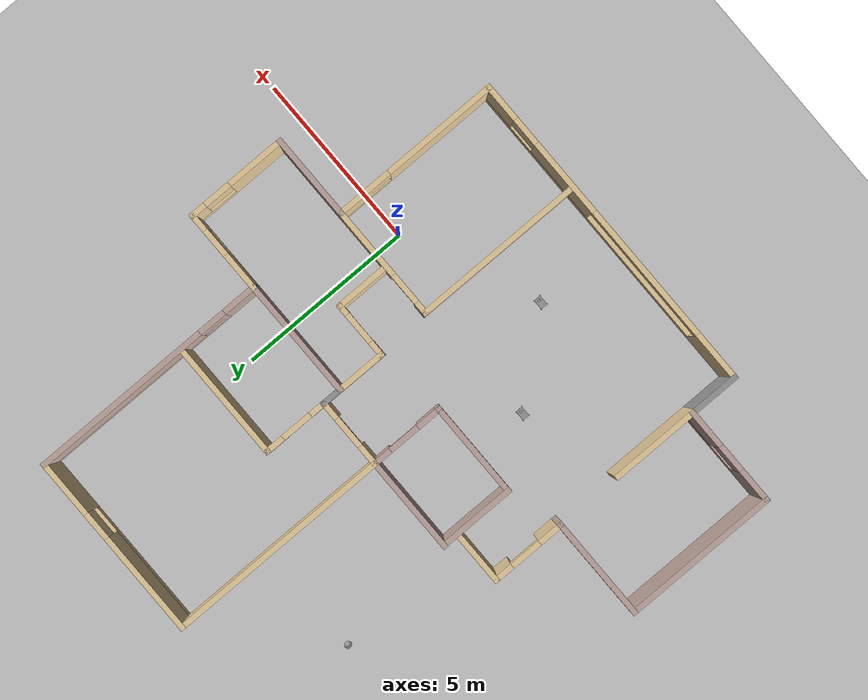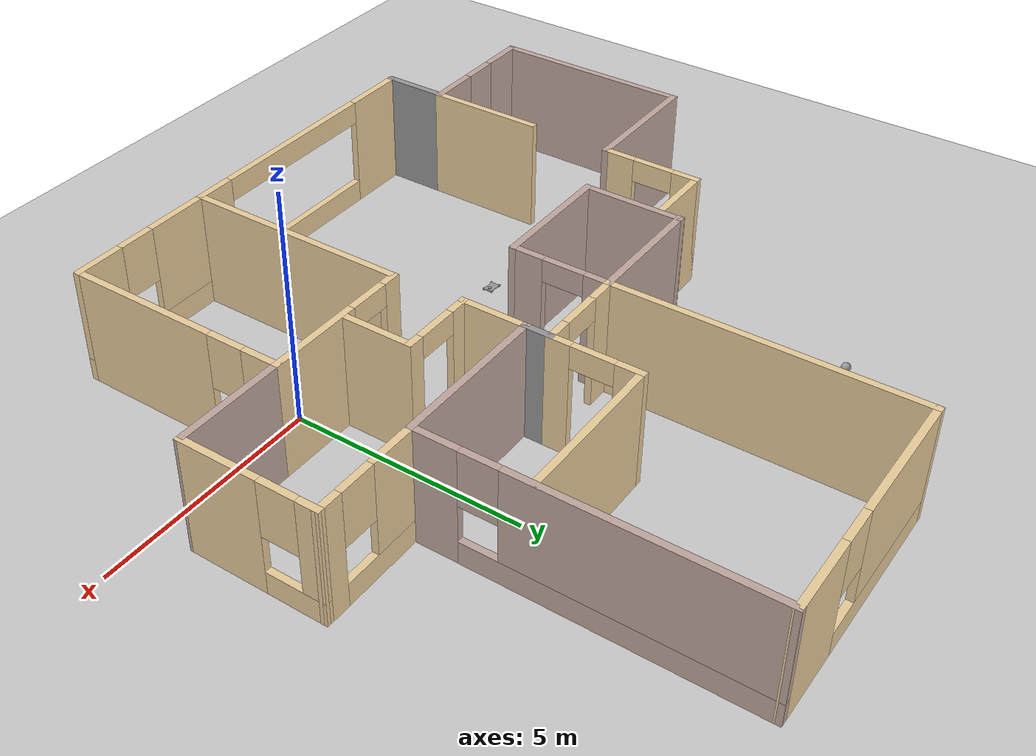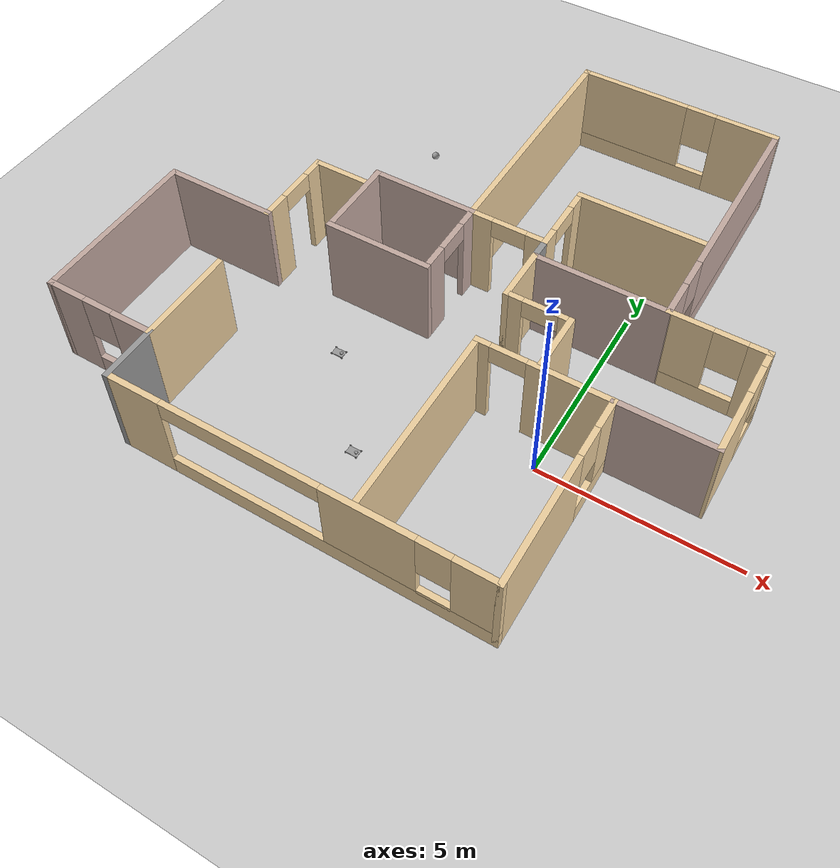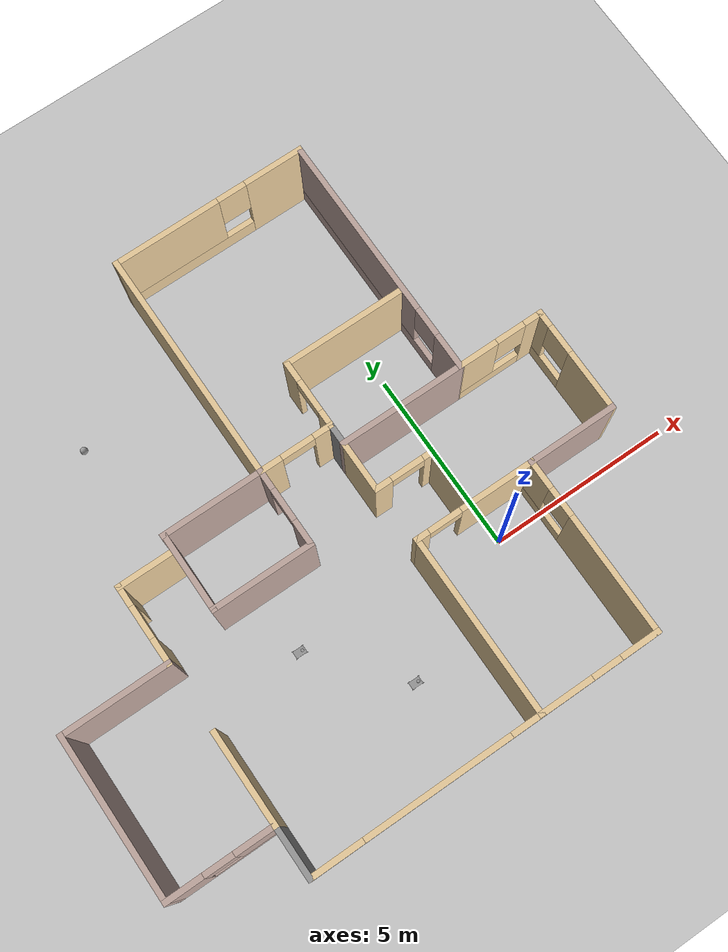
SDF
<sdf version="1.6">
 <world name="default">
  <plugin name="greetings" filename="libgreetings.so"/>
  <light name="sun" type="directional">
   <pose>0 0 10 0 -0 0</pose>
   <diffuse>0.8 0.8 0.8 1</diffuse>
   <specular>0.2 0.2 0.2 1</specular>
   <attenuation>
    <range>1000</range>
    <constant>0.9</constant>
    <linear>0.01</linear>
    <quadratic>0.001</quadratic>
   </attenuation>
   <direction>-0.5 0.1 -0.9</direction>
  </light>
  <model name="ground_plane">
   <static>1</static>
   <link name="link">
    <collision name="collision">
     <geometry><plane><normal>0 0 1</normal><size>100 100</size></plane></geometry>
     <surface><friction><ode><mu>100</mu><mu2>50</mu2></ode></friction></surface>
    </collision>
    <visual name="visual">
     <cast_shadows>0</cast_shadows>
     <geometry><plane><normal>0 0 1</normal><size>100 100</size></plane></geometry>
     <material>
      <script><uri>file://media/materials/scripts/gazebo.material</uri><name>Gazebo/Grey</name></script>
     </material>
    </visual>
   </link>
  </model>
  <gravity>0 0 -9.8</gravity>
  <magnetic_field>6e-06 2.3e-05 -4.2e-05</magnetic_field>
  <atmosphere type="adiabatic"/>
  <physics name="default_physics" default="0" type="ode">
   <max_step_size>0.001</max_step_size>
   <real_time_factor>1</real_time_factor>
   <real_time_update_rate>1000</real_time_update_rate>
  </physics>
  <scene><ambient>0.4 0.4 0.4 1</ambient><background>0.7 0.7 0.7 1</background><shadows>1</shadows></scene>
  <spherical_coordinates>
   <surface_model>EARTH_WGS84</surface_model>
   <latitude_deg>0</latitude_deg>
   <longitude_deg>0</longitude_deg>
   <elevation>0</elevation>
   <heading_deg>0</heading_deg>
  </spherical_coordinates>
  <model name="myrobot">
   <link name="link_0">
    <pose>-0.079072 0.08625 0.009834 0 -0 0</pose>
    <inertial>
     <mass>1</mass>
     <inertia>
      <ixx>0.166667</ixx>
      <ixy>0</ixy>
      <ixz>0</ixz>
      <iyy>0.166667</iyy>
      <iyz>0</iyz>
      <izz>0.166667</izz>
     </inertia>
     <pose>0 0 0.03 0 -0 0</pose>
    </inertial>
    <visual name="visual">
     <pose>0 0 0.03 0 -0 0</pose>
     <geometry><box><size>0.3 0.2 0.02</size></box></geometry>
     <material>
      <lighting>1</lighting>
      <script><uri>file://media/materials/scripts/gazebo.material</uri><name>Gazebo/Grey</name></script>
      <shader type="pixel"><normal_map>__default__</normal_map></shader>
      <ambient>0.3 0.3 0.3 1</ambient>
      <diffuse>0.7 0.7 0.7 1</diffuse>
      <specular>0.01 0.01 0.01 1</specular>
      <emissive>0 0 0 1</emissive>
     </material>
    </visual>
    <collision name="collision">
     <pose>0 0 0.03 0 -0 0</pose>
     <geometry><box><size>0.3 0.2 0.02</size></box></geometry>
     <surface>
      <friction>
       <ode><mu>1</mu><mu2>1</mu2><fdir1>0 0 0</fdir1><slip1>0</slip1><slip2>0</slip2></ode>
       <torsional>
        <coefficient>1</coefficient>
        <patch_radius>0</patch_radius>
        <surface_radius>0</surface_radius>
        <use_patch_radius>1</use_patch_radius>
        <ode><slip>0</slip></ode>
       </torsional>
      </friction>
      <bounce><restitution_coefficient>0</restitution_coefficient><threshold>1e+06</threshold></bounce>
      <contact>
       <collide_without_contact>0</collide_without_contact>
       <collide_without_contact_bitmask>1</collide_without_contact_bitmask>
       <collide_bitmask>1</collide_bitmask>
       <ode>
        <soft_cfm>0</soft_cfm>
        <soft_erp>0.2</soft_erp>
        <kp>1e+13</kp>
        <kd>1</kd>
        <max_vel>0.01</max_vel>
        <min_depth>0</min_depth>
       </ode>
       <bullet>
        <split_impulse>1</split_impulse>
        <split_impulse_penetration_threshold>-0.01</split_impulse_penetration_threshold>
        <soft_cfm>0</soft_cfm>
        <soft_erp>0.2</soft_erp>
        <kp>1e+13</kp>
        <kd>1</kd>
       </bullet>
      </contact>
     </surface>
    </collision>
   </link>
   <link name="link_1">
    <pose>0.060928 -0.01875 0.039833 1.5708 -0 0</pose>
    <inertial>
     <mass>1</mass>
     <inertia><ixx>0.145833</ixx><ixy>0</ixy><ixz>0</ixz><iyy>0.145833</iyy><iyz>0</iyz><izz>0.125</izz></inertia>
    </inertial>
    <visual name="visual">
     <geometry><cylinder><radius>0.03</radius><length>0.01</length></cylinder></geometry>
     <material>
      <lighting>1</lighting>
      <script><uri>file://media/materials/scripts/gazebo.material</uri><name>Gazebo/Grey</name></script>
      <shader type="pixel"><normal_map>__default__</normal_map></shader>
      <ambient>0.3 0.3 0.3 1</ambient>
      <diffuse>0.7 0.7 0.7 1</diffuse>
      <specular>0.01 0.01 0.01 1</specular>
      <emissive>0 0 0 1</emissive>
     </material>
    </visual>
    <collision name="collision">
     <geometry><cylinder><radius>0.03</radius><length>0.01</length></cylinder></geometry>
     <surface>
      <friction>
       <ode><mu>1</mu><mu2>1</mu2><fdir1>0 0 0</fdir1><slip1>0</slip1><slip2>0</slip2></ode>
       <torsional>
        <coefficient>1</coefficient>
        <patch_radius>0</patch_radius>
        <surface_radius>0</surface_radius>
        <use_patch_radius>1</use_patch_radius>
        <ode><slip>0</slip></ode>
       </torsional>
      </friction>
      <bounce><restitution_coefficient>0</restitution_coefficient><threshold>1e+06</threshold></bounce>
      <contact>
       <collide_without_contact>0</collide_without_contact>
       <collide_without_contact_bitmask>1</collide_without_contact_bitmask>
       <collide_bitmask>1</collide_bitmask>
       <ode>
        <soft_cfm>0</soft_cfm>
        <soft_erp>0.2</soft_erp>
        <kp>1e+13</kp>
        <kd>1</kd>
        <max_vel>0.01</max_vel>
        <min_depth>0</min_depth>
       </ode>
       <bullet>
        <split_impulse>1</split_impulse>
        <split_impulse_penetration_threshold>-0.01</split_impulse_penetration_threshold>
        <soft_cfm>0</soft_cfm>
        <soft_erp>0.2</soft_erp>
        <kp>1e+13</kp>
        <kd>1</kd>
       </bullet>
      </contact>
     </surface>
    </collision>
   </link>
   <link name="link_1_clone">
    <pose>-0.219072 -0.01875 0.039833 1.5708 -0 0</pose>
    <inertial>
     <mass>1</mass>
     <inertia><ixx>0.145833</ixx><ixy>0</ixy><ixz>0</ixz><iyy>0.145833</iyy><iyz>0</iyz><izz>0.125</izz></inertia>
    </inertial>
    <visual name="visual">
     <geometry><cylinder><radius>0.03</radius><length>0.01</length></cylinder></geometry>
     <material>
      <lighting>1</lighting>
      <script><uri>file://media/materials/scripts/gazebo.material</uri><name>Gazebo/Grey</name></script>
      <shader type="pixel"><normal_map>__default__</normal_map></shader>
      <ambient>0.3 0.3 0.3 1</ambient>
      <diffuse>0.7 0.7 0.7 1</diffuse>
      <specular>0.01 0.01 0.01 1</specular>
      <emissive>0 0 0 1</emissive>
     </material>
    </visual>
    <collision name="collision">
     <geometry><cylinder><radius>0.03</radius><length>0.01</length></cylinder></geometry>
     <surface>
      <friction>
       <ode><mu>1</mu><mu2>1</mu2><fdir1>0 0 0</fdir1><slip1>0</slip1><slip2>0</slip2></ode>
       <torsional>
        <coefficient>1</coefficient>
        <patch_radius>0</patch_radius>
        <surface_radius>0</surface_radius>
        <use_patch_radius>1</use_patch_radius>
        <ode><slip>0</slip></ode>
       </torsional>
      </friction>
      <bounce><restitution_coefficient>0</restitution_coefficient><threshold>1e+06</threshold></bounce>
      <contact>
       <collide_without_contact>0</collide_without_contact>
       <collide_without_contact_bitmask>1</collide_without_contact_bitmask>
       <collide_bitmask>1</collide_bitmask>
       <ode>
        <soft_cfm>0</soft_cfm>
        <soft_erp>0.2</soft_erp>
        <kp>1e+13</kp>
        <kd>1</kd>
        <max_vel>0.01</max_vel>
        <min_depth>0</min_depth>
       </ode>
       <bullet>
        <split_impulse>1</split_impulse>
        <split_impulse_penetration_threshold>-0.01</split_impulse_penetration_threshold>
        <soft_cfm>0</soft_cfm>
        <soft_erp>0.2</soft_erp>
        <kp>1e+13</kp>
        <kd>1</kd>
       </bullet>
      </contact>
     </surface>
    </collision>
   </link>
   <link name="link_1_clone_0">
    <pose>-0.219072 0.19125 0.039833 1.5708 -0 0</pose>
    <inertial>
     <mass>1</mass>
     <inertia><ixx>0.145833</ixx><ixy>0</ixy><ixz>0</ixz><iyy>0.145833</iyy><iyz>0</iyz><izz>0.125</izz></inertia>
    </inertial>
    <visual name="visual">
     <geometry><cylinder><radius>0.03</radius><length>0.01</length></cylinder></geometry>
     <material>
      <lighting>1</lighting>
      <script><uri>file://media/materials/scripts/gazebo.material</uri><name>Gazebo/Grey</name></script>
      <shader type="pixel"><normal_map>__default__</normal_map></shader>
      <ambient>0.3 0.3 0.3 1</ambient>
      <diffuse>0.7 0.7 0.7 1</diffuse>
      <specular>0.01 0.01 0.01 1</specular>
      <emissive>0 0 0 1</emissive>
     </material>
    </visual>
    <collision name="collision">
     <geometry><cylinder><radius>0.03</radius><length>0.01</length></cylinder></geometry>
     <surface>
      <friction>
       <ode><mu>1</mu><mu2>1</mu2><fdir1>0 0 0</fdir1><slip1>0</slip1><slip2>0</slip2></ode>
       <torsional>
        <coefficient>1</coefficient>
        <patch_radius>0</patch_radius>
        <surface_radius>0</surface_radius>
        <use_patch_radius>1</use_patch_radius>
        <ode><slip>0</slip></ode>
       </torsional>
      </friction>
      <bounce><restitution_coefficient>0</restitution_coefficient><threshold>1e+06</threshold></bounce>
      <contact>
       <collide_without_contact>0</collide_without_contact>
       <collide_without_contact_bitmask>1</collide_without_contact_bitmask>
       <collide_bitmask>1</collide_bitmask>
       <ode>
        <soft_cfm>0</soft_cfm>
        <soft_erp>0.2</soft_erp>
        <kp>1e+13</kp>
        <kd>1</kd>
        <max_vel>0.01</max_vel>
        <min_depth>0</min_depth>
       </ode>
       <bullet>
        <split_impulse>1</split_impulse>
        <split_impulse_penetration_threshold>-0.01</split_impulse_penetration_threshold>
        <soft_cfm>0</soft_cfm>
        <soft_erp>0.2</soft_erp>
        <kp>1e+13</kp>
        <kd>1</kd>
       </bullet>
      </contact>
     </surface>
    </collision>
   </link>
   <link name="link_1_clone_1">
    <pose>0.060928 0.19125 0.039833 1.5708 -0 0</pose>
    <inertial>
     <mass>1</mass>
     <inertia><ixx>0.145833</ixx><ixy>0</ixy><ixz>0</ixz><iyy>0.145833</iyy><iyz>0</iyz><izz>0.125</izz></inertia>
    </inertial>
    <visual name="visual">
     <geometry><cylinder><radius>0.03</radius><length>0.01</length></cylinder></geometry>
     <material>
      <lighting>1</lighting>
      <script><uri>file://media/materials/scripts/gazebo.material</uri><name>Gazebo/Grey</name></script>
      <shader type="pixel"><normal_map>__default__</normal_map></shader>
      <ambient>0.3 0.3 0.3 1</ambient>
      <diffuse>0.7 0.7 0.7 1</diffuse>
      <specular>0.01 0.01 0.01 1</specular>
      <emissive>0 0 0 1</emissive>
     </material>
    </visual>
    <collision name="collision">
     <geometry><cylinder><radius>0.03</radius><length>0.01</length></cylinder></geometry>
     <surface>
      <friction>
       <ode><mu>1</mu><mu2>1</mu2><fdir1>0 0 0</fdir1><slip1>0</slip1><slip2>0</slip2></ode>
       <torsional>
        <coefficient>1</coefficient>
        <patch_radius>0</patch_radius>
        <surface_radius>0</surface_radius>
        <use_patch_radius>1</use_patch_radius>
        <ode><slip>0</slip></ode>
       </torsional>
      </friction>
      <bounce><restitution_coefficient>0</restitution_coefficient><threshold>1e+06</threshold></bounce>
      <contact>
       <collide_without_contact>0</collide_without_contact>
       <collide_without_contact_bitmask>1</collide_without_contact_bitmask>
       <collide_bitmask>1</collide_bitmask>
       <ode>
        <soft_cfm>0</soft_cfm>
        <soft_erp>0.2</soft_erp>
        <kp>1e+13</kp>
        <kd>1</kd>
        <max_vel>0.01</max_vel>
        <min_depth>0</min_depth>
       </ode>
       <bullet>
        <split_impulse>1</split_impulse>
        <split_impulse_penetration_threshold>-0.01</split_impulse_penetration_threshold>
        <soft_cfm>0</soft_cfm>
        <soft_erp>0.2</soft_erp>
        <kp>1e+13</kp>
        <kd>1</kd>
       </bullet>
      </contact>
     </surface>
    </collision>
   </link>
   <link name="link_2">
    <pose>-0.004072 0.08625 0.064834 0 -0 0</pose>
    <inertial>
     <mass>1</mass>
     <inertia><ixx>0.145833</ixx><ixy>0</ixy><ixz>0</ixz><iyy>0.145833</iyy><iyz>0</iyz><izz>0.125</izz></inertia>
    </inertial>
    <visual name="visual">
     <geometry><cylinder><radius>0.04</radius><length>0.03</length></cylinder></geometry>
     <material>
      <lighting>1</lighting>
      <script><uri>file://media/materials/scripts/gazebo.material</uri><name>Gazebo/Grey</name></script>
      <shader type="pixel"><normal_map>__default__</normal_map></shader>
      <ambient>0.3 0.3 0.3 1</ambient>
      <diffuse>0.7 0.7 0.7 1</diffuse>
      <specular>0.01 0.01 0.01 1</specular>
      <emissive>0 0 0 1</emissive>
     </material>
    </visual>
    <collision name="collision">
     <geometry><cylinder><radius>0.04</radius><length>0.03</length></cylinder></geometry>
     <surface>
      <friction>
       <ode><mu>1</mu><mu2>1</mu2><fdir1>0 0 0</fdir1><slip1>0</slip1><slip2>0</slip2></ode>
       <torsional>
        <coefficient>1</coefficient>
        <patch_radius>0</patch_radius>
        <surface_radius>0</surface_radius>
        <use_patch_radius>1</use_patch_radius>
        <ode><slip>0</slip></ode>
       </torsional>
      </friction>
      <bounce><restitution_coefficient>0</restitution_coefficient><threshold>1e+06</threshold></bounce>
      <contact>
       <collide_without_contact>0</collide_without_contact>
       <collide_without_contact_bitmask>1</collide_without_contact_bitmask>
       <collide_bitmask>1</collide_bitmask>
       <ode>
        <soft_cfm>0</soft_cfm>
        <soft_erp>0.2</soft_erp>
        <kp>1e+13</kp>
        <kd>1</kd>
        <max_vel>0.01</max_vel>
        <min_depth>0</min_depth>
       </ode>
       <bullet>
        <split_impulse>1</split_impulse>
        <split_impulse_penetration_threshold>-0.01</split_impulse_penetration_threshold>
        <soft_cfm>0</soft_cfm>
        <soft_erp>0.2</soft_erp>
        <kp>1e+13</kp>
        <kd>1</kd>
       </bullet>
      </contact>
     </surface>
    </collision>
   </link>
   <joint name="link_0_JOINT_0" type="revolute">
    <parent>link_0</parent>
    <child>link_1</child>
    <axis>
     <xyz>0 0 1</xyz>
     <use_parent_model_frame>0</use_parent_model_frame>
     <limit>
      <lower>-1.79769e+308</lower>
      <upper>1.79769e+308</upper>
      <effort>-1</effort>
      <velocity>-1</velocity>
     </limit>
     <dynamics>
      <spring_reference>0</spring_reference>
      <spring_stiffness>0</spring_stiffness>
      <damping>0</damping>
     </dynamics>
    </axis>
    <physics>
     <ode><limit><cfm>0</cfm><erp>0.2</erp></limit><suspension><cfm>0</cfm><erp>0.2</erp></suspension></ode>
    </physics>
   </joint>
   <joint name="link_0_JOINT_1" type="revolute">
    <parent>link_0</parent>
    <child>link_1_clone_1</child>
    <axis>
     <xyz>0 0 1</xyz>
     <use_parent_model_frame>0</use_parent_model_frame>
     <limit>
      <lower>-1.79769e+308</lower>
      <upper>1.79769e+308</upper>
      <effort>-1</effort>
      <velocity>-1</velocity>
     </limit>
     <dynamics>
      <spring_reference>0</spring_reference>
      <spring_stiffness>0</spring_stiffness>
      <damping>0</damping>
     </dynamics>
    </axis>
    <physics>
     <ode><limit><cfm>0</cfm><erp>0.2</erp></limit><suspension><cfm>0</cfm><erp>0.2</erp></suspension></ode>
    </physics>
   </joint>
   <joint name="link_0_JOINT_2" type="revolute">
    <parent>link_0</parent>
    <child>link_1_clone_0</child>
    <axis>
     <xyz>0 0 1</xyz>
     <use_parent_model_frame>0</use_parent_model_frame>
     <limit>
      <lower>-1.79769e+308</lower>
      <upper>1.79769e+308</upper>
      <effort>-1</effort>
      <velocity>-1</velocity>
     </limit>
     <dynamics>
      <spring_reference>0</spring_reference>
      <spring_stiffness>0</spring_stiffness>
      <damping>0</damping>
     </dynamics>
    </axis>
    <physics>
     <ode><limit><cfm>0</cfm><erp>0.2</erp></limit><suspension><cfm>0</cfm><erp>0.2</erp></suspension></ode>
    </physics>
   </joint>
   <joint name="link_0_JOINT_3" type="revolute">
    <parent>link_0</parent>
    <child>link_1_clone</child>
    <axis>
     <xyz>0 0 1</xyz>
     <use_parent_model_frame>0</use_parent_model_frame>
     <limit>
      <lower>-1.79769e+308</lower>
      <upper>1.79769e+308</upper>
      <effort>-1</effort>
      <velocity>-1</velocity>
     </limit>
     <dynamics>
      <spring_reference>0</spring_reference>
      <spring_stiffness>0</spring_stiffness>
      <damping>0</damping>
     </dynamics>
    </axis>
    <physics>
     <ode><limit><cfm>0</cfm><erp>0.2</erp></limit><suspension><cfm>0</cfm><erp>0.2</erp></suspension></ode>
    </physics>
   </joint>
   <joint name="link_0_JOINT_4" type="revolute">
    <parent>link_0</parent>
    <child>link_2</child>
    <axis>
     <xyz>0 0 1</xyz>
     <use_parent_model_frame>0</use_parent_model_frame>
     <limit>
      <lower>-1.79769e+308</lower>
      <upper>1.79769e+308</upper>
      <effort>-1</effort>
      <velocity>-1</velocity>
     </limit>
     <dynamics>
      <spring_reference>0</spring_reference>
      <spring_stiffness>0</spring_stiffness>
      <damping>0</damping>
     </dynamics>
    </axis>
    <physics>
     <ode><limit><cfm>0</cfm><erp>0.2</erp></limit><suspension><cfm>0</cfm><erp>0.2</erp></suspension></ode>
    </physics>
   </joint>
   <static>0</static>
   <pose>-5.50984 0.448397 -0.009833 0 0 -0.000488</pose>
  </model>
  <model name="mybuilding">
   <pose>-3.71799 3.23906 0 0 -0 0</pose>
   <link name="Wall_11">
    <pose>-4.49901 -0.527557 0 0 0 -1.5708</pose>
    <visual name="Wall_11_Visual_0">
     <pose>-0.829746 0 1.25 0 -0 0</pose>
     <geometry><box><size>0.605509 0.15 2.5</size></box></geometry>
     <material>
      <script><uri>file://media/materials/scripts/gazebo.material</uri><name>Gazebo/Grey</name></script>
      <ambient>0.921569 0.807843 0.615686 1</ambient>
     </material>
     <meta><layer>0</layer></meta>
    </visual>
    <collision name="Wall_11_Collision_0">
     <geometry><box><size>0.605509 0.15 2.5</size></box></geometry>
     <pose>-0.829746 0 1.25 0 -0 0</pose>
    </collision>
    <visual name="Wall_11_Visual_1">
     <pose>0.752754 0 1.25 0 -0 0</pose>
     <geometry><box><size>0.759491 0.15 2.5</size></box></geometry>
     <material>
      <script><uri>file://media/materials/scripts/gazebo.material</uri><name>Gazebo/Grey</name></script>
      <ambient>0.921569 0.807843 0.615686 1</ambient>
     </material>
     <meta><layer>0</layer></meta>
    </visual>
    <collision name="Wall_11_Collision_1">
     <geometry><box><size>0.759491 0.15 2.5</size></box></geometry>
     <pose>0.752754 0 1.25 0 -0 0</pose>
    </collision>
    <visual name="Wall_11_Visual_2">
     <pose>-0.076991 0 2.25 0 -0 0</pose>
     <geometry><box><size>0.9 0.15 0.5</size></box></geometry>
     <material>
      <script><uri>file://media/materials/scripts/gazebo.material</uri><name>Gazebo/Grey</name></script>
      <ambient>0.921569 0.807843 0.615686 1</ambient>
     </material>
     <meta><layer>0</layer></meta>
    </visual>
    <collision name="Wall_11_Collision_2">
     <geometry><box><size>0.9 0.15 0.5</size></box></geometry>
     <pose>-0.076991 0 2.25 0 -0 0</pose>
    </collision>
   </link>
   <link name="Wall_12">
    <collision name="Wall_12_Collision">
     <geometry><box><size>3 0.15 2.5</size></box></geometry>
     <pose>0 0 1.25 0 -0 0</pose>
    </collision>
    <visual name="Wall_12_Visual">
     <pose>0 0 1.25 0 -0 0</pose>
     <geometry><box><size>3 0.15 2.5</size></box></geometry>
     <material>
      <script><uri>file://media/materials/scripts/gazebo.material</uri><name>Gazebo/Grey</name></script>
      <ambient>0.760784 0.662745 0.627451 1</ambient>
     </material>
     <meta><layer>0</layer></meta>
    </visual>
    <pose>-5.92401 -1.58506 0 0 -0 3.14159</pose>
   </link>
   <link name="Wall_13">
    <collision name="Wall_13_Collision">
     <geometry><box><size>4.48 0.15 2.5</size></box></geometry>
     <pose>0 0 1.25 0 -0 0</pose>
    </collision>
    <visual name="Wall_13_Visual">
     <pose>0 0 1.25 0 -0 0</pose>
     <geometry><box><size>4.48 0.15 2.5</size></box></geometry>
     <material>
      <script><uri>file://media/materials/scripts/gazebo.material</uri><name>Gazebo/Grey</name></script>
      <ambient>0.760784 0.662745 0.627451 1</ambient>
     </material>
     <meta><layer>0</layer></meta>
    </visual>
    <pose>-7.34901 -3.75006 0 0 0 -1.5708</pose>
   </link>
   <link name="Wall_14">
    <pose>-5.92401 -5.91506 0 0 -0 0</pose>
    <visual name="Wall_14_Visual_0">
     <pose>-0.977046 0 1.25 0 -0 0</pose>
     <geometry><box><size>1.04591 0.15 2.5</size></box></geometry>
     <material>
      <script><uri>file://media/materials/scripts/gazebo.material</uri><name>Gazebo/Grey</name></script>
      <ambient>0.760784 0.662745 0.627451 1</ambient>
     </material>
     <meta><layer>0</layer></meta>
    </visual>
    <collision name="Wall_14_Collision_0">
     <geometry><box><size>1.04591 0.15 2.5</size></box></geometry>
     <pose>-0.977046 0 1.25 0 -0 0</pose>
    </collision>
    <visual name="Wall_14_Visual_1">
     <pose>0.522954 0 0.25 0 -0 0</pose>
     <geometry><box><size>1.95409 0.15 0.5</size></box></geometry>
     <material>
      <script><uri>file://media/materials/scripts/gazebo.material</uri><name>Gazebo/Grey</name></script>
      <ambient>0.760784 0.662745 0.627451 1</ambient>
     </material>
     <meta><layer>0</layer></meta>
    </visual>
    <collision name="Wall_14_Collision_1">
     <geometry><box><size>1.95409 0.15 0.5</size></box></geometry>
     <pose>0.522954 0 0.25 0 -0 0</pose>
    </collision>
    <visual name="Wall_14_Visual_2">
     <pose>0.922954 0 1.5 0 -0 0</pose>
     <geometry><box><size>1.15409 0.15 2</size></box></geometry>
     <material>
      <script><uri>file://media/materials/scripts/gazebo.material</uri><name>Gazebo/Grey</name></script>
      <ambient>0.760784 0.662745 0.627451 1</ambient>
     </material>
     <meta><layer>0</layer></meta>
    </visual>
    <collision name="Wall_14_Collision_2">
     <geometry><box><size>1.15409 0.15 2</size></box></geometry>
     <pose>0.922954 0 1.5 0 -0 0</pose>
    </collision>
    <visual name="Wall_14_Visual_3">
     <pose>-0.054091 0 1.9 0 -0 0</pose>
     <geometry><box><size>0.8 0.15 1.2</size></box></geometry>
     <material>
      <script><uri>file://media/materials/scripts/gazebo.material</uri><name>Gazebo/Grey</name></script>
      <ambient>0.760784 0.662745 0.627451 1</ambient>
     </material>
     <meta><layer>0</layer></meta>
    </visual>
    <collision name="Wall_14_Collision_3">
     <geometry><box><size>0.8 0.15 1.2</size></box></geometry>
     <pose>-0.054091 0 1.9 0 -0 0</pose>
    </collision>
   </link>
   <link name="Wall_15">
    <collision name="Wall_15_Collision">
     <geometry><box><size>1.52 0.15 2.5</size></box></geometry>
     <pose>0 0 1.25 0 -0 0</pose>
    </collision>
    <visual name="Wall_15_Visual">
     <pose>0 0 1.25 0 -0 0</pose>
     <geometry><box><size>1.52 0.15 2.5</size></box></geometry>
     <material>
      <script><uri>file://media/materials/scripts/gazebo.material</uri><name>Gazebo/Grey</name></script>
      <ambient>1 1 1 1</ambient>
     </material>
     <meta><layer>0</layer></meta>
    </visual>
    <pose>-4.49901 -6.60006 0 0 0 -1.5708</pose>
   </link>
   <link name="Wall_16">
    <pose>0.249487 -7.28506 0 0 -0 0</pose>
    <visual name="Wall_16_Visual_0">
     <pose>-4.07389 0 1.25 0 -0 0</pose>
     <geometry><box><size>1.49958 0.15 2.5</size></box></geometry>
     <material>
      <script><uri>file://media/materials/scripts/gazebo.material</uri><name>Gazebo/Grey</name></script>
      <ambient>0.921569 0.807843 0.615686 1</ambient>
     </material>
     <meta><layer>0</layer></meta>
    </visual>
    <collision name="Wall_16_Collision_0">
     <geometry><box><size>1.49958 0.15 2.5</size></box></geometry>
     <pose>-4.07389 0 1.25 0 -0 0</pose>
    </collision>
    <visual name="Wall_16_Visual_1">
     <pose>0.74979 0 0.25 0 -0 0</pose>
     <geometry><box><size>8.14778 0.15 0.5</size></box></geometry>
     <material>
      <script><uri>file://media/materials/scripts/gazebo.material</uri><name>Gazebo/Grey</name></script>
      <ambient>0.921569 0.807843 0.615686 1</ambient>
     </material>
     <meta><layer>0</layer></meta>
    </visual>
    <collision name="Wall_16_Collision_1">
     <geometry><box><size>8.14778 0.15 0.5</size></box></geometry>
     <pose>0.74979 0 0.25 0 -0 0</pose>
    </collision>
    <visual name="Wall_16_Visual_2">
     <pose>1.79558 0 1.5 0 -0 0</pose>
     <geometry><box><size>2.23937 0.15 2</size></box></geometry>
     <material>
      <script><uri>file://media/materials/scripts/gazebo.material</uri><name>Gazebo/Grey</name></script>
      <ambient>0.921569 0.807843 0.615686 1</ambient>
     </material>
     <meta><layer>0</layer></meta>
    </visual>
    <collision name="Wall_16_Collision_2">
     <geometry><box><size>2.23937 0.15 2</size></box></geometry>
     <pose>1.79558 0 1.5 0 -0 0</pose>
    </collision>
    <visual name="Wall_16_Visual_3">
     <pose>4.26947 0 1.5 0 -0 0</pose>
     <geometry><box><size>1.10841 0.15 2</size></box></geometry>
     <material>
      <script><uri>file://media/materials/scripts/gazebo.material</uri><name>Gazebo/Grey</name></script>
      <ambient>0.921569 0.807843 0.615686 1</ambient>
     </material>
     <meta><layer>0</layer></meta>
    </visual>
    <collision name="Wall_16_Collision_3">
     <geometry><box><size>1.10841 0.15 2</size></box></geometry>
     <pose>4.26947 0 1.5 0 -0 0</pose>
    </collision>
    <visual name="Wall_16_Visual_4">
     <pose>3.31527 0 0.5 0 -0 0</pose>
     <geometry><box><size>0.8 0.15 0.1</size></box></geometry>
     <material>
      <script><uri>file://media/materials/scripts/gazebo.material</uri><name>Gazebo/Grey</name></script>
      <ambient>0.921569 0.807843 0.615686 1</ambient>
     </material>
     <meta><layer>0</layer></meta>
    </visual>
    <collision name="Wall_16_Collision_4">
     <geometry><box><size>0.8 0.15 0.1</size></box></geometry>
     <pose>3.31527 0 0.5 0 -0 0</pose>
    </collision>
    <visual name="Wall_16_Visual_5">
     <pose>3.31527 0 1.9 0 -0 0</pose>
     <geometry><box><size>0.8 0.15 1.2</size></box></geometry>
     <material>
      <script><uri>file://media/materials/scripts/gazebo.material</uri><name>Gazebo/Grey</name></script>
      <ambient>0.921569 0.807843 0.615686 1</ambient>
     </material>
     <meta><layer>0</layer></meta>
    </visual>
    <collision name="Wall_16_Collision_5">
     <geometry><box><size>0.8 0.15 1.2</size></box></geometry>
     <pose>3.31527 0 1.9 0 -0 0</pose>
    </collision>
    <visual name="Wall_16_Visual_6">
     <pose>-1.3241 0 2.25 0 -0 0</pose>
     <geometry><box><size>4 0.15 0.5</size></box></geometry>
     <material>
      <script><uri>file://media/materials/scripts/gazebo.material</uri><name>Gazebo/Grey</name></script>
      <ambient>0.921569 0.807843 0.615686 1</ambient>
     </material>
     <meta><layer>0</layer></meta>
    </visual>
    <collision name="Wall_16_Collision_6">
     <geometry><box><size>4 0.15 0.5</size></box></geometry>
     <pose>-1.3241 0 2.25 0 -0 0</pose>
    </collision>
   </link>
   <link name="Wall_17">
    <pose>4.99799 -4.86006 0 0 -0 1.5708</pose>
    <visual name="Wall_17_Visual_0">
     <pose>-0.82328 0 1.25 0 -0 0</pose>
     <geometry><box><size>3.35344 0.15 2.5</size></box></geometry>
     <material>
      <script><uri>file://media/materials/scripts/gazebo.material</uri><name>Gazebo/Grey</name></script>
      <ambient>0.921569 0.807843 0.615686 1</ambient>
     </material>
     <meta><layer>0</layer></meta>
    </visual>
    <collision name="Wall_17_Collision_0">
     <geometry><box><size>3.35344 0.15 2.5</size></box></geometry>
     <pose>-0.82328 0 1.25 0 -0 0</pose>
    </collision>
    <visual name="Wall_17_Visual_1">
     <pose>1.67672 0 0.25 0 -0 0</pose>
     <geometry><box><size>1.64656 0.15 0.5</size></box></geometry>
     <material>
      <script><uri>file://media/materials/scripts/gazebo.material</uri><name>Gazebo/Grey</name></script>
      <ambient>0.921569 0.807843 0.615686 1</ambient>
     </material>
     <meta><layer>0</layer></meta>
    </visual>
    <collision name="Wall_17_Collision_1">
     <geometry><box><size>1.64656 0.15 0.5</size></box></geometry>
     <pose>1.67672 0 0.25 0 -0 0</pose>
    </collision>
    <visual name="Wall_17_Visual_2">
     <pose>2.07672 0 1.5 0 -0 0</pose>
     <geometry><box><size>0.84656 0.15 2</size></box></geometry>
     <material>
      <script><uri>file://media/materials/scripts/gazebo.material</uri><name>Gazebo/Grey</name></script>
      <ambient>0.921569 0.807843 0.615686 1</ambient>
     </material>
     <meta><layer>0</layer></meta>
    </visual>
    <collision name="Wall_17_Collision_2">
     <geometry><box><size>0.84656 0.15 2</size></box></geometry>
     <pose>2.07672 0 1.5 0 -0 0</pose>
    </collision>
    <visual name="Wall_17_Visual_3">
     <pose>1.25344 0 1.9 0 -0 0</pose>
     <geometry><box><size>0.8 0.15 1.2</size></box></geometry>
     <material>
      <script><uri>file://media/materials/scripts/gazebo.material</uri><name>Gazebo/Grey</name></script>
      <ambient>0.921569 0.807843 0.615686 1</ambient>
     </material>
     <meta><layer>0</layer></meta>
    </visual>
    <collision name="Wall_17_Collision_3">
     <geometry><box><size>0.8 0.15 1.2</size></box></geometry>
     <pose>1.25344 0 1.9 0 -0 0</pose>
    </collision>
   </link>
   <link name="Wall_18">
    <collision name="Wall_18_Collision">
     <geometry><box><size>2.5 0.15 2.5</size></box></geometry>
     <pose>0 0 1.25 0 -0 0</pose>
    </collision>
    <visual name="Wall_18_Visual">
     <pose>0 0 1.25 0 -0 0</pose>
     <geometry><box><size>2.5 0.15 2.5</size></box></geometry>
     <material>
      <script><uri>file://media/materials/scripts/gazebo.material</uri><name>Gazebo/Grey</name></script>
      <ambient>0.760784 0.662745 0.627451 1</ambient>
     </material>
     <meta><layer>0</layer></meta>
    </visual>
    <pose>6.17299 -2.43506 0 0 -0 0</pose>
   </link>
   <link name="Wall_19">
    <pose>7.34849 -1.00006 0 0 -0 1.57045</pose>
    <visual name="Wall_19_Visual_0">
     <pose>-0.641701 0 1.25 0 -0 0</pose>
     <geometry><box><size>1.7366 0.15 2.5</size></box></geometry>
     <material>
      <script><uri>file://media/materials/scripts/gazebo.material</uri><name>Gazebo/Grey</name></script>
      <ambient>0.921569 0.807843 0.615686 1</ambient>
     </material>
     <meta><layer>0</layer></meta>
    </visual>
    <collision name="Wall_19_Collision_0">
     <geometry><box><size>1.7366 0.15 2.5</size></box></geometry>
     <pose>-0.641701 0 1.25 0 -0 0</pose>
    </collision>
    <visual name="Wall_19_Visual_1">
     <pose>0.868299 0 0.25 0 -0 0</pose>
     <geometry><box><size>1.2834 0.15 0.5</size></box></geometry>
     <material>
      <script><uri>file://media/materials/scripts/gazebo.material</uri><name>Gazebo/Grey</name></script>
      <ambient>0.921569 0.807843 0.615686 1</ambient>
     </material>
     <meta><layer>0</layer></meta>
    </visual>
    <collision name="Wall_19_Collision_1">
     <geometry><box><size>1.2834 0.15 0.5</size></box></geometry>
     <pose>0.868299 0 0.25 0 -0 0</pose>
    </collision>
    <visual name="Wall_19_Visual_2">
     <pose>1.2683 0 1.5 0 -0 0</pose>
     <geometry><box><size>0.483401 0.15 2</size></box></geometry>
     <material>
      <script><uri>file://media/materials/scripts/gazebo.material</uri><name>Gazebo/Grey</name></script>
      <ambient>0.921569 0.807843 0.615686 1</ambient>
     </material>
     <meta><layer>0</layer></meta>
    </visual>
    <collision name="Wall_19_Collision_2">
     <geometry><box><size>0.483401 0.15 2</size></box></geometry>
     <pose>1.2683 0 1.5 0 -0 0</pose>
    </collision>
    <visual name="Wall_19_Visual_3">
     <pose>0.626599 0 1.9 0 -0 0</pose>
     <geometry><box><size>0.8 0.15 1.2</size></box></geometry>
     <material>
      <script><uri>file://media/materials/scripts/gazebo.material</uri><name>Gazebo/Grey</name></script>
      <ambient>0.921569 0.807843 0.615686 1</ambient>
     </material>
     <meta><layer>0</layer></meta>
    </visual>
    <collision name="Wall_19_Collision_3">
     <geometry><box><size>0.8 0.15 1.2</size></box></geometry>
     <pose>0.626599 0 1.9 0 -0 0</pose>
    </collision>
   </link>
   <link name="Wall_20">
    <pose>6.17349 0.434943 0 0 -0 3.14159</pose>
    <visual name="Wall_20_Visual_0">
     <pose>-0.969557 0 1.25 0 -0 0</pose>
     <geometry><box><size>0.561885 0.15 2.5</size></box></geometry>
     <material>
      <script><uri>file://media/materials/scripts/gazebo.material</uri><name>Gazebo/Grey</name></script>
      <ambient>0.921569 0.807843 0.615686 1</ambient>
     </material>
     <meta><layer>0</layer></meta>
    </visual>
    <collision name="Wall_20_Collision_0">
     <geometry><box><size>0.561885 0.15 2.5</size></box></geometry>
     <pose>-0.969557 0 1.25 0 -0 0</pose>
    </collision>
    <visual name="Wall_20_Visual_1">
     <pose>0.280943 0 0.25 0 -0 0</pose>
     <geometry><box><size>1.93911 0.15 0.5</size></box></geometry>
     <material>
      <script><uri>file://media/materials/scripts/gazebo.material</uri><name>Gazebo/Grey</name></script>
      <ambient>0.921569 0.807843 0.615686 1</ambient>
     </material>
     <meta><layer>0</layer></meta>
    </visual>
    <collision name="Wall_20_Collision_1">
     <geometry><box><size>1.93911 0.15 0.5</size></box></geometry>
     <pose>0.280943 0 0.25 0 -0 0</pose>
    </collision>
    <visual name="Wall_20_Visual_2">
     <pose>0.680943 0 1.5 0 -0 0</pose>
     <geometry><box><size>1.13912 0.15 2</size></box></geometry>
     <material>
      <script><uri>file://media/materials/scripts/gazebo.material</uri><name>Gazebo/Grey</name></script>
      <ambient>0.921569 0.807843 0.615686 1</ambient>
     </material>
     <meta><layer>0</layer></meta>
    </visual>
    <collision name="Wall_20_Collision_2">
     <geometry><box><size>1.13912 0.15 2</size></box></geometry>
     <pose>0.680943 0 1.5 0 -0 0</pose>
    </collision>
    <visual name="Wall_20_Visual_3">
     <pose>-0.288615 0 1.9 0 -0 0</pose>
     <geometry><box><size>0.8 0.15 1.2</size></box></geometry>
     <material>
      <script><uri>file://media/materials/scripts/gazebo.material</uri><name>Gazebo/Grey</name></script>
      <ambient>0.921569 0.807843 0.615686 1</ambient>
     </material>
     <meta><layer>0</layer></meta>
    </visual>
    <collision name="Wall_20_Collision_3">
     <geometry><box><size>0.8 0.15 1.2</size></box></geometry>
     <pose>-0.288615 0 1.9 0 -0 0</pose>
    </collision>
   </link>
   <link name="Wall_21">
    <pose>4.99849 3.85994 0 0 -0 1.57065</pose>
    <visual name="Wall_21_Visual_0">
     <pose>-2.9828 0 1.25 0 -0 0</pose>
     <geometry><box><size>1.03439 0.15 2.5</size></box></geometry>
     <material>
      <script><uri>file://media/materials/scripts/gazebo.material</uri><name>Gazebo/Grey</name></script>
      <ambient>0.760784 0.662745 0.627451 1</ambient>
     </material>
     <meta><layer>0</layer></meta>
    </visual>
    <collision name="Wall_21_Collision_0">
     <geometry><box><size>1.03439 0.15 2.5</size></box></geometry>
     <pose>-2.9828 0 1.25 0 -0 0</pose>
    </collision>
    <visual name="Wall_21_Visual_1">
     <pose>0.517195 0 0.25 0 -0 0</pose>
     <geometry><box><size>5.96561 0.15 0.5</size></box></geometry>
     <material>
      <script><uri>file://media/materials/scripts/gazebo.material</uri><name>Gazebo/Grey</name></script>
      <ambient>0.760784 0.662745 0.627451 1</ambient>
     </material>
     <meta><layer>0</layer></meta>
    </visual>
    <collision name="Wall_21_Collision_1">
     <geometry><box><size>5.96561 0.15 0.5</size></box></geometry>
     <pose>0.517195 0 0.25 0 -0 0</pose>
    </collision>
    <visual name="Wall_21_Visual_2">
     <pose>0.917195 0 1.5 0 -0 0</pose>
     <geometry><box><size>5.16561 0.15 2</size></box></geometry>
     <material>
      <script><uri>file://media/materials/scripts/gazebo.material</uri><name>Gazebo/Grey</name></script>
      <ambient>0.760784 0.662745 0.627451 1</ambient>
     </material>
     <meta><layer>0</layer></meta>
    </visual>
    <collision name="Wall_21_Collision_2">
     <geometry><box><size>5.16561 0.15 2</size></box></geometry>
     <pose>0.917195 0 1.5 0 -0 0</pose>
    </collision>
    <visual name="Wall_21_Visual_3">
     <pose>-2.06561 0 1.9 0 -0 0</pose>
     <geometry><box><size>0.8 0.15 1.2</size></box></geometry>
     <material>
      <script><uri>file://media/materials/scripts/gazebo.material</uri><name>Gazebo/Grey</name></script>
      <ambient>0.760784 0.662745 0.627451 1</ambient>
     </material>
     <meta><layer>0</layer></meta>
    </visual>
    <collision name="Wall_21_Collision_3">
     <geometry><box><size>0.8 0.15 1.2</size></box></geometry>
     <pose>-2.06561 0 1.9 0 -0 0</pose>
    </collision>
   </link>
   <link name="Wall_22">
    <pose>2.33549 7.28494 0 0 -0 3.14159</pose>
    <visual name="Wall_22_Visual_0">
     <pose>-1.89349 0 1.25 0 -0 0</pose>
     <geometry><box><size>1.69001 0.15 2.5</size></box></geometry>
     <material>
      <script><uri>file://media/materials/scripts/gazebo.material</uri><name>Gazebo/Grey</name></script>
      <ambient>0.921569 0.807843 0.615686 1</ambient>
     </material>
     <meta><layer>0</layer></meta>
    </visual>
    <collision name="Wall_22_Collision_0">
     <geometry><box><size>1.69001 0.15 2.5</size></box></geometry>
     <pose>-1.89349 0 1.25 0 -0 0</pose>
    </collision>
    <visual name="Wall_22_Visual_1">
     <pose>0.845005 0 0.25 0 -0 0</pose>
     <geometry><box><size>3.78699 0.15 0.5</size></box></geometry>
     <material>
      <script><uri>file://media/materials/scripts/gazebo.material</uri><name>Gazebo/Grey</name></script>
      <ambient>0.921569 0.807843 0.615686 1</ambient>
     </material>
     <meta><layer>0</layer></meta>
    </visual>
    <collision name="Wall_22_Collision_1">
     <geometry><box><size>3.78699 0.15 0.5</size></box></geometry>
     <pose>0.845005 0 0.25 0 -0 0</pose>
    </collision>
    <visual name="Wall_22_Visual_2">
     <pose>1.245 0 1.5 0 -0 0</pose>
     <geometry><box><size>2.98699 0.15 2</size></box></geometry>
     <material>
      <script><uri>file://media/materials/scripts/gazebo.material</uri><name>Gazebo/Grey</name></script>
      <ambient>0.921569 0.807843 0.615686 1</ambient>
     </material>
     <meta><layer>0</layer></meta>
    </visual>
    <collision name="Wall_22_Collision_2">
     <geometry><box><size>2.98699 0.15 2</size></box></geometry>
     <pose>1.245 0 1.5 0 -0 0</pose>
    </collision>
    <visual name="Wall_22_Visual_3">
     <pose>-0.648491 0 1.9 0 -0 0</pose>
     <geometry><box><size>0.8 0.15 1.2</size></box></geometry>
     <material>
      <script><uri>file://media/materials/scripts/gazebo.material</uri><name>Gazebo/Grey</name></script>
      <ambient>0.921569 0.807843 0.615686 1</ambient>
     </material>
     <meta><layer>0</layer></meta>
    </visual>
    <collision name="Wall_22_Collision_3">
     <geometry><box><size>0.8 0.15 1.2</size></box></geometry>
     <pose>-0.648491 0 1.9 0 -0 0</pose>
    </collision>
   </link>
   <link name="Wall_23">
    <collision name="Wall_23_Collision">
     <geometry><box><size>6.46823 0.15 2.5</size></box></geometry>
     <pose>0 0 1.25 0 -0 0</pose>
    </collision>
    <visual name="Wall_23_Visual">
     <pose>0 0 1.25 0 -0 0</pose>
     <geometry><box><size>6.46823 0.15 2.5</size></box></geometry>
     <material>
      <script><uri>file://media/materials/scripts/gazebo.material</uri><name>Gazebo/Grey</name></script>
      <ambient>0.921569 0.807843 0.615686 1</ambient>
     </material>
     <meta><layer>0</layer></meta>
    </visual>
    <pose>-0.328013 4.12594 0 0 0 -1.5708</pose>
   </link>
   <link name="Wall_24">
    <collision name="Wall_24_Collision">
     <geometry><box><size>2.83849 0.15 2.5</size></box></geometry>
     <pose>0 0 1.25 0 -0 0</pose>
    </collision>
    <visual name="Wall_24_Visual">
     <pose>0 0 1.25 0 -0 0</pose>
     <geometry><box><size>2.83849 0.15 2.5</size></box></geometry>
     <material>
      <script><uri>file://media/materials/scripts/gazebo.material</uri><name>Gazebo/Grey</name></script>
      <ambient>0.760784 0.662745 0.627451 1</ambient>
     </material>
     <meta><layer>0</layer></meta>
    </visual>
    <pose>-1.67226 0.966851 0 0 0 -3.14152</pose>
   </link>
   <link name="Wall_25">
    <collision name="Wall_25_Collision">
     <geometry><box><size>2.24882 0.15 2.5</size></box></geometry>
     <pose>0 0 1.25 0 -0 0</pose>
    </collision>
    <visual name="Wall_25_Visual">
     <pose>0 0 1.25 0 -0 0</pose>
     <geometry><box><size>2.24882 0.15 2.5</size></box></geometry>
     <material>
      <script><uri>file://media/materials/scripts/gazebo.material</uri><name>Gazebo/Grey</name></script>
      <ambient>0.760784 0.662745 0.627451 1</ambient>
     </material>
     <meta><layer>0</layer></meta>
    </visual>
    <pose>-2.99901 -0.082649 0 0 0 -1.5708</pose>
   </link>
   <link name="Wall_29">
    <collision name="Wall_29_Collision">
     <geometry><box><size>2.6 0.15 2.5</size></box></geometry>
     <pose>0 0 1.25 0 -0 0</pose>
    </collision>
    <visual name="Wall_29_Visual">
     <pose>0 0 1.25 0 -0 0</pose>
     <geometry><box><size>2.6 0.15 2.5</size></box></geometry>
     <material>
      <script><uri>file://media/materials/scripts/gazebo.material</uri><name>Gazebo/Grey</name></script>
      <ambient>0.921569 0.807843 0.615686 1</ambient>
     </material>
     <meta><layer>0</layer></meta>
    </visual>
    <pose>-4.49901 -4.69006 0 0 -0 1.5708</pose>
   </link>
   <link name="Wall_32">
    <collision name="Wall_32_Collision">
     <geometry><box><size>4.99 0.15 2.5</size></box></geometry>
     <pose>0 0 1.25 0 -0 0</pose>
    </collision>
    <visual name="Wall_32_Visual">
     <pose>0 0 1.25 0 -0 0</pose>
     <geometry><box><size>4.99 0.15 2.5</size></box></geometry>
     <material>
      <script><uri>file://media/materials/scripts/gazebo.material</uri><name>Gazebo/Grey</name></script>
      <ambient>0.921569 0.807843 0.615686 1</ambient>
     </material>
     <meta><layer>0</layer></meta>
    </visual>
    <pose>1.73699 -4.85506 0 0 -0 1.5708</pose>
   </link>
   <link name="Wall_33">
    <pose>3.36749 -2.43506 0 0 -0 0</pose>
    <visual name="Wall_33_Visual_0">
     <pose>-1.50168 0 1.25 0 -0 0</pose>
     <geometry><box><size>0.408074 0.15 2.5</size></box></geometry>
     <material>
      <script><uri>file://media/materials/scripts/gazebo.material</uri><name>Gazebo/Grey</name></script>
      <ambient>0.921569 0.807843 0.615686 1</ambient>
     </material>
     <meta><layer>0</layer></meta>
    </visual>
    <collision name="Wall_33_Collision_0">
     <geometry><box><size>0.408074 0.15 2.5</size></box></geometry>
     <pose>-1.50168 0 1.25 0 -0 0</pose>
    </collision>
    <visual name="Wall_33_Visual_1">
     <pose>0.654037 0 1.25 0 -0 0</pose>
     <geometry><box><size>2.10337 0.15 2.5</size></box></geometry>
     <material>
      <script><uri>file://media/materials/scripts/gazebo.material</uri><name>Gazebo/Grey</name></script>
      <ambient>0.921569 0.807843 0.615686 1</ambient>
     </material>
     <meta><layer>0</layer></meta>
    </visual>
    <collision name="Wall_33_Collision_1">
     <geometry><box><size>2.10337 0.15 2.5</size></box></geometry>
     <pose>0.654037 0 1.25 0 -0 0</pose>
    </collision>
    <visual name="Wall_33_Visual_2">
     <pose>-0.847648 0 2.25 0 -0 0</pose>
     <geometry><box><size>0.9 0.15 0.5</size></box></geometry>
     <material>
      <script><uri>file://media/materials/scripts/gazebo.material</uri><name>Gazebo/Grey</name></script>
      <ambient>0.921569 0.807843 0.615686 1</ambient>
     </material>
     <meta><layer>0</layer></meta>
    </visual>
    <collision name="Wall_33_Collision_2">
     <geometry><box><size>0.9 0.15 0.5</size></box></geometry>
     <pose>-0.847648 0 2.25 0 -0 0</pose>
    </collision>
   </link>
   <link name="Wall_35">
    <collision name="Wall_35_Collision">
     <geometry><box><size>3.5 0.15 2.5</size></box></geometry>
     <pose>0 0 1.25 0 -0 0</pose>
    </collision>
    <visual name="Wall_35_Visual">
     <pose>0 0 1.25 0 -0 0</pose>
     <geometry><box><size>3.5 0.15 2.5</size></box></geometry>
     <material>
      <script><uri>file://media/materials/scripts/gazebo.material</uri><name>Gazebo/Grey</name></script>
      <ambient>0.760784 0.662745 0.627451 1</ambient>
     </material>
     <meta><layer>0</layer></meta>
    </visual>
    <pose>3.32299 0.434943 0 0 -0 3.14159</pose>
   </link>
   <link name="Wall_36">
    <collision name="Wall_36_Collision">
     <geometry><box><size>1.5 0.15 2.5</size></box></geometry>
     <pose>0 0 1.25 0 -0 0</pose>
    </collision>
    <visual name="Wall_36_Visual">
     <pose>0 0 1.25 0 -0 0</pose>
     <geometry><box><size>1.5 0.15 2.5</size></box></geometry>
     <material>
      <script><uri>file://media/materials/scripts/gazebo.material</uri><name>Gazebo/Grey</name></script>
      <ambient>0.921569 0.807843 0.615686 1</ambient>
     </material>
     <meta><layer>0</layer></meta>
    </visual>
    <pose>1.64799 -0.240057 0 0 0 -1.5708</pose>
   </link>
   <link name="Wall_37">
    <pose>2.44799 -0.915057 0 0 -0 0</pose>
    <visual name="Wall_37_Visual_0">
     <pose>-0.629356 0 1.25 0 -0 0</pose>
     <geometry><box><size>0.491288 0.15 2.5</size></box></geometry>
     <material>
      <script><uri>file://media/materials/scripts/gazebo.material</uri><name>Gazebo/Grey</name></script>
      <ambient>0.921569 0.807843 0.615686 1</ambient>
     </material>
     <meta><layer>0</layer></meta>
    </visual>
    <collision name="Wall_37_Collision_0">
     <geometry><box><size>0.491288 0.15 2.5</size></box></geometry>
     <pose>-0.629356 0 1.25 0 -0 0</pose>
    </collision>
    <visual name="Wall_37_Visual_1">
     <pose>0.695644 0 1.25 0 -0 0</pose>
     <geometry><box><size>0.358712 0.15 2.5</size></box></geometry>
     <material>
      <script><uri>file://media/materials/scripts/gazebo.material</uri><name>Gazebo/Grey</name></script>
      <ambient>0.921569 0.807843 0.615686 1</ambient>
     </material>
     <meta><layer>0</layer></meta>
    </visual>
    <collision name="Wall_37_Collision_1">
     <geometry><box><size>0.358712 0.15 2.5</size></box></geometry>
     <pose>0.695644 0 1.25 0 -0 0</pose>
    </collision>
    <visual name="Wall_37_Visual_2">
     <pose>0.066288 0 2.25 0 -0 0</pose>
     <geometry><box><size>0.9 0.15 0.5</size></box></geometry>
     <material>
      <script><uri>file://media/materials/scripts/gazebo.material</uri><name>Gazebo/Grey</name></script>
      <ambient>0.921569 0.807843 0.615686 1</ambient>
     </material>
     <meta><layer>0</layer></meta>
    </visual>
    <collision name="Wall_37_Collision_2">
     <geometry><box><size>0.9 0.15 0.5</size></box></geometry>
     <pose>0.066288 0 2.25 0 -0 0</pose>
    </collision>
   </link>
   <link name="Wall_38">
    <collision name="Wall_38_Collision">
     <geometry><box><size>1.55 0.15 2.5</size></box></geometry>
     <pose>0 0 1.25 0 -0 0</pose>
    </collision>
    <visual name="Wall_38_Visual">
     <pose>0 0 1.25 0 -0 0</pose>
     <geometry><box><size>1.55 0.15 2.5</size></box></geometry>
     <material>
      <script><uri>file://media/materials/scripts/gazebo.material</uri><name>Gazebo/Grey</name></script>
      <ambient>0.921569 0.807843 0.615686 1</ambient>
     </material>
     <meta><layer>0</layer></meta>
    </visual>
    <pose>3.24799 -1.61506 0 0 0 -1.5708</pose>
   </link>
   <link name="Wall_88">
    <collision name="Wall_88_Collision">
     <geometry><box><size>2.82135 0.15 2.5</size></box></geometry>
     <pose>0 0 1.25 0 -0 0</pose>
    </collision>
    <visual name="Wall_88_Visual">
     <pose>0 0 1.25 0 -0 0</pose>
     <geometry><box><size>2.82135 0.15 2.5</size></box></geometry>
     <material>
      <script><uri>file://media/materials/scripts/gazebo.material</uri><name>Gazebo/Grey</name></script>
      <ambient>0.760784 0.662745 0.627451 1</ambient>
     </material>
     <meta><layer>0</layer></meta>
    </visual>
    <pose>-1.66351 -1.13206 0 0 -0 0</pose>
   </link>
   <link name="Wall_89">
    <pose>-0.328013 -0.082556 0 0 -0 1.5708</pose>
    <visual name="Wall_89_Visual_0">
     <pose>-0.743113 0 1.25 0 -0 0</pose>
     <geometry><box><size>0.762589 0.15 2.5</size></box></geometry>
     <material>
      <script><uri>file://media/materials/scripts/gazebo.material</uri><name>Gazebo/Grey</name></script>
      <ambient>0.760784 0.662745 0.627451 1</ambient>
     </material>
     <meta><layer>0</layer></meta>
    </visual>
    <collision name="Wall_89_Collision_0">
     <geometry><box><size>0.762589 0.15 2.5</size></box></geometry>
     <pose>-0.743113 0 1.25 0 -0 0</pose>
    </collision>
    <visual name="Wall_89_Visual_1">
     <pose>0.831295 0 1.25 0 -0 0</pose>
     <geometry><box><size>0.586226 0.15 2.5</size></box></geometry>
     <material>
      <script><uri>file://media/materials/scripts/gazebo.material</uri><name>Gazebo/Grey</name></script>
      <ambient>0.760784 0.662745 0.627451 1</ambient>
     </material>
     <meta><layer>0</layer></meta>
    </visual>
    <collision name="Wall_89_Collision_1">
     <geometry><box><size>0.586226 0.15 2.5</size></box></geometry>
     <pose>0.831295 0 1.25 0 -0 0</pose>
    </collision>
    <visual name="Wall_89_Visual_2">
     <pose>0.088182 0 2.25 0 -0 0</pose>
     <geometry><box><size>0.9 0.15 0.5</size></box></geometry>
     <material>
      <script><uri>file://media/materials/scripts/gazebo.material</uri><name>Gazebo/Grey</name></script>
      <ambient>0.760784 0.662745 0.627451 1</ambient>
     </material>
     <meta><layer>0</layer></meta>
    </visual>
    <collision name="Wall_89_Collision_2">
     <geometry><box><size>0.9 0.15 0.5</size></box></geometry>
     <pose>0.088182 0 2.25 0 -0 0</pose>
    </collision>
   </link>
   <link name="Wall_91">
    <collision name="Wall_91_Collision">
     <geometry><box><size>0.682541 0.15 2.5</size></box></geometry>
     <pose>0 0 1.25 0 -0 0</pose>
    </collision>
    <visual name="Wall_91_Visual">
     <pose>0 0 1.25 0 -0 0</pose>
     <geometry><box><size>0.682541 0.15 2.5</size></box></geometry>
     <material>
      <script><uri>file://media/materials/scripts/gazebo.material</uri><name>Gazebo/Grey</name></script>
      <ambient>1 1 1 1</ambient>
     </material>
     <meta><layer>0</layer></meta>
    </visual>
    <pose>1.64799 0.700943 0 0 -0 1.5708</pose>
   </link>
   <link name="Wall_92">
    <pose>0.659987 0.966943 0 0 -0 3.14159</pose>
    <visual name="Wall_92_Visual_0">
     <pose>-0.775821 0 1.25 0 -0 0</pose>
     <geometry><box><size>0.574357 0.15 2.5</size></box></geometry>
     <material>
      <script><uri>file://media/materials/scripts/gazebo.material</uri><name>Gazebo/Grey</name></script>
      <ambient>0.921569 0.807843 0.615686 1</ambient>
     </material>
     <meta><layer>0</layer></meta>
    </visual>
    <collision name="Wall_92_Collision_0">
     <geometry><box><size>0.574357 0.15 2.5</size></box></geometry>
     <pose>-0.775821 0 1.25 0 -0 0</pose>
    </collision>
    <visual name="Wall_92_Visual_1">
     <pose>0.737179 0 1.25 0 -0 0</pose>
     <geometry><box><size>0.651643 0.15 2.5</size></box></geometry>
     <material>
      <script><uri>file://media/materials/scripts/gazebo.material</uri><name>Gazebo/Grey</name></script>
      <ambient>0.921569 0.807843 0.615686 1</ambient>
     </material>
     <meta><layer>0</layer></meta>
    </visual>
    <collision name="Wall_92_Collision_1">
     <geometry><box><size>0.651643 0.15 2.5</size></box></geometry>
     <pose>0.737179 0 1.25 0 -0 0</pose>
    </collision>
    <visual name="Wall_92_Visual_2">
     <pose>-0.038643 0 2.25 0 -0 0</pose>
     <geometry><box><size>0.9 0.15 0.5</size></box></geometry>
     <material>
      <script><uri>file://media/materials/scripts/gazebo.material</uri><name>Gazebo/Grey</name></script>
      <ambient>0.921569 0.807843 0.615686 1</ambient>
     </material>
     <meta><layer>0</layer></meta>
    </visual>
    <collision name="Wall_92_Collision_2">
     <geometry><box><size>0.9 0.15 0.5</size></box></geometry>
     <pose>-0.038643 0 2.25 0 -0 0</pose>
    </collision>
   </link>
   <link name="Wall_94">
    <collision name="Wall_94_Collision">
     <geometry><box><size>1.5 0.15 2.5</size></box></geometry>
     <pose>0 0 1.25 0 -0 0</pose>
    </collision>
    <visual name="Wall_94_Visual">
     <pose>0 0 1.25 0 -0 0</pose>
     <geometry><box><size>1.5 0.15 2.5</size></box></geometry>
     <material>
      <script><uri>file://media/materials/scripts/gazebo.material</uri><name>Gazebo/Grey</name></script>
      <ambient>0.921569 0.807843 0.615686 1</ambient>
     </material>
     <meta><layer>0</layer></meta>
    </visual>
    <pose>-3.82401 0.529943 0 0 -0 0</pose>
   </link>
   <link name="Wall_96">
    <pose>1.64799 1.89194 0 0 -0 1.5708</pose>
    <visual name="Wall_96_Visual_0">
     <pose>-0.743821 0 1.25 0 -0 0</pose>
     <geometry><box><size>0.512358 0.15 2.5</size></box></geometry>
     <material>
      <script><uri>file://media/materials/scripts/gazebo.material</uri><name>Gazebo/Grey</name></script>
      <ambient>0.921569 0.807843 0.615686 1</ambient>
     </material>
     <meta><layer>0</layer></meta>
    </visual>
    <collision name="Wall_96_Collision_0">
     <geometry><box><size>0.512358 0.15 2.5</size></box></geometry>
     <pose>-0.743821 0 1.25 0 -0 0</pose>
    </collision>
    <visual name="Wall_96_Visual_1">
     <pose>0.706179 0 1.25 0 -0 0</pose>
     <geometry><box><size>0.587642 0.15 2.5</size></box></geometry>
     <material>
      <script><uri>file://media/materials/scripts/gazebo.material</uri><name>Gazebo/Grey</name></script>
      <ambient>0.921569 0.807843 0.615686 1</ambient>
     </material>
     <meta><layer>0</layer></meta>
    </visual>
    <collision name="Wall_96_Collision_1">
     <geometry><box><size>0.587642 0.15 2.5</size></box></geometry>
     <pose>0.706179 0 1.25 0 -0 0</pose>
    </collision>
    <visual name="Wall_96_Visual_2">
     <pose>-0.037642 0 2.25 0 -0 0</pose>
     <geometry><box><size>0.9 0.15 0.5</size></box></geometry>
     <material>
      <script><uri>file://media/materials/scripts/gazebo.material</uri><name>Gazebo/Grey</name></script>
      <ambient>0.921569 0.807843 0.615686 1</ambient>
     </material>
     <meta><layer>0</layer></meta>
    </visual>
    <collision name="Wall_96_Collision_2">
     <geometry><box><size>0.9 0.15 0.5</size></box></geometry>
     <pose>-0.037642 0 2.25 0 -0 0</pose>
    </collision>
   </link>
   <link name="Wall_97">
    <collision name="Wall_97_Collision">
     <geometry><box><size>3.5 0.15 2.5</size></box></geometry>
     <pose>0 0 1.25 0 -0 0</pose>
    </collision>
    <visual name="Wall_97_Visual">
     <pose>0 0 1.25 0 -0 0</pose>
     <geometry><box><size>3.5 0.15 2.5</size></box></geometry>
     <material>
      <script><uri>file://media/materials/scripts/gazebo.material</uri><name>Gazebo/Grey</name></script>
      <ambient>0.921569 0.807843 0.615686 1</ambient>
     </material>
     <meta><layer>0</layer></meta>
    </visual>
    <pose>3.32299 2.81694 0 0 -0 0</pose>
   </link>
   <static>1</static>
  </model>
  <model name="myrobot_clone">
   <link name="link_0">
    <pose>-0.079072 0.08625 0.009834 0 -0 0</pose>
    <inertial>
     <mass>1</mass>
     <inertia>
      <ixx>0.166667</ixx>
      <ixy>0</ixy>
      <ixz>0</ixz>
      <iyy>0.166667</iyy>
      <iyz>0</iyz>
      <izz>0.166667</izz>
     </inertia>
     <pose>0 0 0.03 0 -0 0</pose>
    </inertial>
    <visual name="visual">
     <pose>0 0 0.03 0 -0 0</pose>
     <geometry><box><size>0.3 0.2 0.02</size></box></geometry>
     <material>
      <lighting>1</lighting>
      <script><uri>file://media/materials/scripts/gazebo.material</uri><name>Gazebo/Grey</name></script>
      <shader type="pixel"><normal_map>__default__</normal_map></shader>
      <ambient>0.3 0.3 0.3 1</ambient>
      <diffuse>0.7 0.7 0.7 1</diffuse>
      <specular>0.01 0.01 0.01 1</specular>
      <emissive>0 0 0 1</emissive>
     </material>
    </visual>
    <collision name="collision">
     <pose>0 0 0.03 0 -0 0</pose>
     <geometry><box><size>0.3 0.2 0.02</size></box></geometry>
     <surface>
      <friction>
       <ode><mu>1</mu><mu2>1</mu2><fdir1>0 0 0</fdir1><slip1>0</slip1><slip2>0</slip2></ode>
       <torsional>
        <coefficient>1</coefficient>
        <patch_radius>0</patch_radius>
        <surface_radius>0</surface_radius>
        <use_patch_radius>1</use_patch_radius>
        <ode><slip>0</slip></ode>
       </torsional>
      </friction>
      <bounce><restitution_coefficient>0</restitution_coefficient><threshold>1e+06</threshold></bounce>
      <contact>
       <collide_without_contact>0</collide_without_contact>
       <collide_without_contact_bitmask>1</collide_without_contact_bitmask>
       <collide_bitmask>1</collide_bitmask>
       <ode>
        <soft_cfm>0</soft_cfm>
        <soft_erp>0.2</soft_erp>
        <kp>1e+13</kp>
        <kd>1</kd>
        <max_vel>0.01</max_vel>
        <min_depth>0</min_depth>
       </ode>
       <bullet>
        <split_impulse>1</split_impulse>
        <split_impulse_penetration_threshold>-0.01</split_impulse_penetration_threshold>
        <soft_cfm>0</soft_cfm>
        <soft_erp>0.2</soft_erp>
        <kp>1e+13</kp>
        <kd>1</kd>
       </bullet>
      </contact>
     </surface>
    </collision>
   </link>
   <link name="link_1">
    <pose>0.060928 -0.01875 0.039833 1.5708 -0 0</pose>
    <inertial>
     <mass>1</mass>
     <inertia><ixx>0.145833</ixx><ixy>0</ixy><ixz>0</ixz><iyy>0.145833</iyy><iyz>0</iyz><izz>0.125</izz></inertia>
    </inertial>
    <visual name="visual">
     <geometry><cylinder><radius>0.03</radius><length>0.01</length></cylinder></geometry>
     <material>
      <lighting>1</lighting>
      <script><uri>file://media/materials/scripts/gazebo.material</uri><name>Gazebo/Grey</name></script>
      <shader type="pixel"><normal_map>__default__</normal_map></shader>
      <ambient>0.3 0.3 0.3 1</ambient>
      <diffuse>0.7 0.7 0.7 1</diffuse>
      <specular>0.01 0.01 0.01 1</specular>
      <emissive>0 0 0 1</emissive>
     </material>
    </visual>
    <collision name="collision">
     <geometry><cylinder><radius>0.03</radius><length>0.01</length></cylinder></geometry>
     <surface>
      <friction>
       <ode><mu>1</mu><mu2>1</mu2><fdir1>0 0 0</fdir1><slip1>0</slip1><slip2>0</slip2></ode>
       <torsional>
        <coefficient>1</coefficient>
        <patch_radius>0</patch_radius>
        <surface_radius>0</surface_radius>
        <use_patch_radius>1</use_patch_radius>
        <ode><slip>0</slip></ode>
       </torsional>
      </friction>
      <bounce><restitution_coefficient>0</restitution_coefficient><threshold>1e+06</threshold></bounce>
      <contact>
       <collide_without_contact>0</collide_without_contact>
       <collide_without_contact_bitmask>1</collide_without_contact_bitmask>
       <collide_bitmask>1</collide_bitmask>
       <ode>
        <soft_cfm>0</soft_cfm>
        <soft_erp>0.2</soft_erp>
        <kp>1e+13</kp>
        <kd>1</kd>
        <max_vel>0.01</max_vel>
        <min_depth>0</min_depth>
       </ode>
       <bullet>
        <split_impulse>1</split_impulse>
        <split_impulse_penetration_threshold>-0.01</split_impulse_penetration_threshold>
        <soft_cfm>0</soft_cfm>
        <soft_erp>0.2</soft_erp>
        <kp>1e+13</kp>
        <kd>1</kd>
       </bullet>
      </contact>
     </surface>
    </collision>
   </link>
   <link name="link_1_clone">
    <pose>-0.219072 -0.01875 0.039833 1.5708 -0 0</pose>
    <inertial>
     <mass>1</mass>
     <inertia><ixx>0.145833</ixx><ixy>0</ixy><ixz>0</ixz><iyy>0.145833</iyy><iyz>0</iyz><izz>0.125</izz></inertia>
    </inertial>
    <visual name="visual">
     <geometry><cylinder><radius>0.03</radius><length>0.01</length></cylinder></geometry>
     <material>
      <lighting>1</lighting>
      <script><uri>file://media/materials/scripts/gazebo.material</uri><name>Gazebo/Grey</name></script>
      <shader type="pixel"><normal_map>__default__</normal_map></shader>
      <ambient>0.3 0.3 0.3 1</ambient>
      <diffuse>0.7 0.7 0.7 1</diffuse>
      <specular>0.01 0.01 0.01 1</specular>
      <emissive>0 0 0 1</emissive>
     </material>
    </visual>
    <collision name="collision">
     <geometry><cylinder><radius>0.03</radius><length>0.01</length></cylinder></geometry>
     <surface>
      <friction>
       <ode><mu>1</mu><mu2>1</mu2><fdir1>0 0 0</fdir1><slip1>0</slip1><slip2>0</slip2></ode>
       <torsional>
        <coefficient>1</coefficient>
        <patch_radius>0</patch_radius>
        <surface_radius>0</surface_radius>
        <use_patch_radius>1</use_patch_radius>
        <ode><slip>0</slip></ode>
       </torsional>
      </friction>
      <bounce><restitution_coefficient>0</restitution_coefficient><threshold>1e+06</threshold></bounce>
      <contact>
       <collide_without_contact>0</collide_without_contact>
       <collide_without_contact_bitmask>1</collide_without_contact_bitmask>
       <collide_bitmask>1</collide_bitmask>
       <ode>
        <soft_cfm>0</soft_cfm>
        <soft_erp>0.2</soft_erp>
        <kp>1e+13</kp>
        <kd>1</kd>
        <max_vel>0.01</max_vel>
        <min_depth>0</min_depth>
       </ode>
       <bullet>
        <split_impulse>1</split_impulse>
        <split_impulse_penetration_threshold>-0.01</split_impulse_penetration_threshold>
        <soft_cfm>0</soft_cfm>
        <soft_erp>0.2</soft_erp>
        <kp>1e+13</kp>
        <kd>1</kd>
       </bullet>
      </contact>
     </surface>
    </collision>
   </link>
   <link name="link_1_clone_0">
    <pose>-0.219072 0.19125 0.039833 1.5708 -0 0</pose>
    <inertial>
     <mass>1</mass>
     <inertia><ixx>0.145833</ixx><ixy>0</ixy><ixz>0</ixz><iyy>0.145833</iyy><iyz>0</iyz><izz>0.125</izz></inertia>
    </inertial>
    <visual name="visual">
     <geometry><cylinder><radius>0.03</radius><length>0.01</length></cylinder></geometry>
     <material>
      <lighting>1</lighting>
      <script><uri>file://media/materials/scripts/gazebo.material</uri><name>Gazebo/Grey</name></script>
      <shader type="pixel"><normal_map>__default__</normal_map></shader>
      <ambient>0.3 0.3 0.3 1</ambient>
      <diffuse>0.7 0.7 0.7 1</diffuse>
      <specular>0.01 0.01 0.01 1</specular>
      <emissive>0 0 0 1</emissive>
     </material>
    </visual>
    <collision name="collision">
     <geometry><cylinder><radius>0.03</radius><length>0.01</length></cylinder></geometry>
     <surface>
      <friction>
       <ode><mu>1</mu><mu2>1</mu2><fdir1>0 0 0</fdir1><slip1>0</slip1><slip2>0</slip2></ode>
       <torsional>
        <coefficient>1</coefficient>
        <patch_radius>0</patch_radius>
        <surface_radius>0</surface_radius>
        <use_patch_radius>1</use_patch_radius>
        <ode><slip>0</slip></ode>
       </torsional>
      </friction>
      <bounce><restitution_coefficient>0</restitution_coefficient><threshold>1e+06</threshold></bounce>
      <contact>
       <collide_without_contact>0</collide_without_contact>
       <collide_without_contact_bitmask>1</collide_without_contact_bitmask>
       <collide_bitmask>1</collide_bitmask>
       <ode>
        <soft_cfm>0</soft_cfm>
        <soft_erp>0.2</soft_erp>
        <kp>1e+13</kp>
        <kd>1</kd>
        <max_vel>0.01</max_vel>
        <min_depth>0</min_depth>
       </ode>
       <bullet>
        <split_impulse>1</split_impulse>
        <split_impulse_penetration_threshold>-0.01</split_impulse_penetration_threshold>
        <soft_cfm>0</soft_cfm>
        <soft_erp>0.2</soft_erp>
        <kp>1e+13</kp>
        <kd>1</kd>
       </bullet>
      </contact>
     </surface>
    </collision>
   </link>
   <link name="link_1_clone_1">
    <pose>0.060928 0.19125 0.039833 1.5708 -0 0</pose>
    <inertial>
     <mass>1</mass>
     <inertia><ixx>0.145833</ixx><ixy>0</ixy><ixz>0</ixz><iyy>0.145833</iyy><iyz>0</iyz><izz>0.125</izz></inertia>
    </inertial>
    <visual name="visual">
     <geometry><cylinder><radius>0.03</radius><length>0.01</length></cylinder></geometry>
     <material>
      <lighting>1</lighting>
      <script><uri>file://media/materials/scripts/gazebo.material</uri><name>Gazebo/Grey</name></script>
      <shader type="pixel"><normal_map>__default__</normal_map></shader>
      <ambient>0.3 0.3 0.3 1</ambient>
      <diffuse>0.7 0.7 0.7 1</diffuse>
      <specular>0.01 0.01 0.01 1</specular>
      <emissive>0 0 0 1</emissive>
     </material>
    </visual>
    <collision name="collision">
     <geometry><cylinder><radius>0.03</radius><length>0.01</length></cylinder></geometry>
     <surface>
      <friction>
       <ode><mu>1</mu><mu2>1</mu2><fdir1>0 0 0</fdir1><slip1>0</slip1><slip2>0</slip2></ode>
       <torsional>
        <coefficient>1</coefficient>
        <patch_radius>0</patch_radius>
        <surface_radius>0</surface_radius>
        <use_patch_radius>1</use_patch_radius>
        <ode><slip>0</slip></ode>
       </torsional>
      </friction>
      <bounce><restitution_coefficient>0</restitution_coefficient><threshold>1e+06</threshold></bounce>
      <contact>
       <collide_without_contact>0</collide_without_contact>
       <collide_without_contact_bitmask>1</collide_without_contact_bitmask>
       <collide_bitmask>1</collide_bitmask>
       <ode>
        <soft_cfm>0</soft_cfm>
        <soft_erp>0.2</soft_erp>
        <kp>1e+13</kp>
        <kd>1</kd>
        <max_vel>0.01</max_vel>
        <min_depth>0</min_depth>
       </ode>
       <bullet>
        <split_impulse>1</split_impulse>
        <split_impulse_penetration_threshold>-0.01</split_impulse_penetration_threshold>
        <soft_cfm>0</soft_cfm>
        <soft_erp>0.2</soft_erp>
        <kp>1e+13</kp>
        <kd>1</kd>
       </bullet>
      </contact>
     </surface>
    </collision>
   </link>
   <link name="link_2">
    <pose>-0.004072 0.08625 0.064834 0 -0 0</pose>
    <inertial>
     <mass>1</mass>
     <inertia><ixx>0.145833</ixx><ixy>0</ixy><ixz>0</ixz><iyy>0.145833</iyy><iyz>0</iyz><izz>0.125</izz></inertia>
    </inertial>
    <visual name="visual">
     <geometry><cylinder><radius>0.04</radius><length>0.03</length></cylinder></geometry>
     <material>
      <lighting>1</lighting>
      <script><uri>file://media/materials/scripts/gazebo.material</uri><name>Gazebo/Grey</name></script>
      <shader type="pixel"><normal_map>__default__</normal_map></shader>
      <ambient>0.3 0.3 0.3 1</ambient>
      <diffuse>0.7 0.7 0.7 1</diffuse>
      <specular>0.01 0.01 0.01 1</specular>
      <emissive>0 0 0 1</emissive>
     </material>
    </visual>
    <collision name="collision">
     <geometry><cylinder><radius>0.04</radius><length>0.03</length></cylinder></geometry>
     <surface>
      <friction>
       <ode><mu>1</mu><mu2>1</mu2><fdir1>0 0 0</fdir1><slip1>0</slip1><slip2>0</slip2></ode>
       <torsional>
        <coefficient>1</coefficient>
        <patch_radius>0</patch_radius>
        <surface_radius>0</surface_radius>
        <use_patch_radius>1</use_patch_radius>
        <ode><slip>0</slip></ode>
       </torsional>
      </friction>
      <bounce><restitution_coefficient>0</restitution_coefficient><threshold>1e+06</threshold></bounce>
      <contact>
       <collide_without_contact>0</collide_without_contact>
       <collide_without_contact_bitmask>1</collide_without_contact_bitmask>
       <collide_bitmask>1</collide_bitmask>
       <ode>
        <soft_cfm>0</soft_cfm>
        <soft_erp>0.2</soft_erp>
        <kp>1e+13</kp>
        <kd>1</kd>
        <max_vel>0.01</max_vel>
        <min_depth>0</min_depth>
       </ode>
       <bullet>
        <split_impulse>1</split_impulse>
        <split_impulse_penetration_threshold>-0.01</split_impulse_penetration_threshold>
        <soft_cfm>0</soft_cfm>
        <soft_erp>0.2</soft_erp>
        <kp>1e+13</kp>
        <kd>1</kd>
       </bullet>
      </contact>
     </surface>
    </collision>
   </link>
   <joint name="link_0_JOINT_0" type="revolute">
    <parent>link_0</parent>
    <child>link_1</child>
    <axis>
     <xyz>0 0 1</xyz>
     <use_parent_model_frame>0</use_parent_model_frame>
     <limit>
      <lower>-1.79769e+308</lower>
      <upper>1.79769e+308</upper>
      <effort>-1</effort>
      <velocity>-1</velocity>
     </limit>
     <dynamics>
      <spring_reference>0</spring_reference>
      <spring_stiffness>0</spring_stiffness>
      <damping>0</damping>
     </dynamics>
    </axis>
    <physics>
     <ode><limit><cfm>0</cfm><erp>0.2</erp></limit><suspension><cfm>0</cfm><erp>0.2</erp></suspension></ode>
    </physics>
   </joint>
   <joint name="link_0_JOINT_1" type="revolute">
    <parent>link_0</parent>
    <child>link_1_clone_1</child>
    <axis>
     <xyz>0 0 1</xyz>
     <use_parent_model_frame>0</use_parent_model_frame>
     <limit>
      <lower>-1.79769e+308</lower>
      <upper>1.79769e+308</upper>
      <effort>-1</effort>
      <velocity>-1</velocity>
     </limit>
     <dynamics>
      <spring_reference>0</spring_reference>
      <spring_stiffness>0</spring_stiffness>
      <damping>0</damping>
     </dynamics>
    </axis>
    <physics>
     <ode><limit><cfm>0</cfm><erp>0.2</erp></limit><suspension><cfm>0</cfm><erp>0.2</erp></suspension></ode>
    </physics>
   </joint>
   <joint name="link_0_JOINT_2" type="revolute">
    <parent>link_0</parent>
    <child>link_1_clone_0</child>
    <axis>
     <xyz>0 0 1</xyz>
     <use_parent_model_frame>0</use_parent_model_frame>
     <limit>
      <lower>-1.79769e+308</lower>
      <upper>1.79769e+308</upper>
      <effort>-1</effort>
      <velocity>-1</velocity>
     </limit>
     <dynamics>
      <spring_reference>0</spring_reference>
      <spring_stiffness>0</spring_stiffness>
      <damping>0</damping>
     </dynamics>
    </axis>
    <physics>
     <ode><limit><cfm>0</cfm><erp>0.2</erp></limit><suspension><cfm>0</cfm><erp>0.2</erp></suspension></ode>
    </physics>
   </joint>
   <joint name="link_0_JOINT_3" type="revolute">
    <parent>link_0</parent>
    <child>link_1_clone</child>
    <axis>
     <xyz>0 0 1</xyz>
     <use_parent_model_frame>0</use_parent_model_frame>
     <limit>
      <lower>-1.79769e+308</lower>
      <upper>1.79769e+308</upper>
      <effort>-1</effort>
      <velocity>-1</velocity>
     </limit>
     <dynamics>
      <spring_reference>0</spring_reference>
      <spring_stiffness>0</spring_stiffness>
      <damping>0</damping>
     </dynamics>
    </axis>
    <physics>
     <ode><limit><cfm>0</cfm><erp>0.2</erp></limit><suspension><cfm>0</cfm><erp>0.2</erp></suspension></ode>
    </physics>
   </joint>
   <joint name="link_0_JOINT_4" type="revolute">
    <parent>link_0</parent>
    <child>link_2</child>
    <axis>
     <xyz>0 0 1</xyz>
     <use_parent_model_frame>0</use_parent_model_frame>
     <limit>
      <lower>-1.79769e+308</lower>
      <upper>1.79769e+308</upper>
      <effort>-1</effort>
      <velocity>-1</velocity>
     </limit>
     <dynamics>
      <spring_reference>0</spring_reference>
      <spring_stiffness>0</spring_stiffness>
      <damping>0</damping>
     </dynamics>
    </axis>
    <physics>
     <ode><limit><cfm>0</cfm><erp>0.2</erp></limit><suspension><cfm>0</cfm><erp>0.2</erp></suspension></ode>
    </physics>
   </joint>
   <static>0</static>
   <pose>-3.61871 -1.77273 -0.009834 -0 4e-06 -0.000496</pose>
  </model>
  <model name="my_ball">
   <link name="link_0">
    <inertial>
     <mass>1</mass>
     <inertia><ixx>0.1</ixx><ixy>0</ixy><ixz>0</ixz><iyy>0.1</iyy><iyz>0</iyz><izz>0.1</izz></inertia>
    </inertial>
    <visual name="visual">
     <geometry><sphere><radius>0.1</radius></sphere></geometry>
     <material>
      <lighting>1</lighting>
      <script><uri>file://media/materials/scripts/gazebo.material</uri><name>Gazebo/Grey</name></script>
      <shader type="pixel"><normal_map>__default__</normal_map></shader>
      <ambient>1 1 1 1</ambient>
      <diffuse>1 1 1 1</diffuse>
      <specular>1 1 1 1</specular>
      <emissive>1 1 1 1</emissive>
     </material>
    </visual>
    <collision name="collision">
     <geometry><sphere><radius>0.1</radius></sphere></geometry>
     <surface>
      <friction>
       <ode><mu>1</mu><mu2>1</mu2><fdir1>0 0 0</fdir1><slip1>0</slip1><slip2>0</slip2></ode>
       <torsional>
        <coefficient>1</coefficient>
        <patch_radius>0</patch_radius>
        <surface_radius>0</surface_radius>
        <use_patch_radius>1</use_patch_radius>
        <ode><slip>0</slip></ode>
       </torsional>
      </friction>
      <bounce><restitution_coefficient>0</restitution_coefficient><threshold>1e+06</threshold></bounce>
      <contact>
       <collide_without_contact>0</collide_without_contact>
       <collide_without_contact_bitmask>1</collide_without_contact_bitmask>
       <collide_bitmask>1</collide_bitmask>
       <ode>
        <soft_cfm>0</soft_cfm>
        <soft_erp>0.2</soft_erp>
        <kp>1e+13</kp>
        <kd>1</kd>
        <max_vel>0.01</max_vel>
        <min_depth>0</min_depth>
       </ode>
       <bullet>
        <split_impulse>1</split_impulse>
        <split_impulse_penetration_threshold>-0.01</split_impulse_penetration_threshold>
        <soft_cfm>0</soft_cfm>
        <soft_erp>0.2</soft_erp>
        <kp>1e+13</kp>
        <kd>1</kd>
       </bullet>
      </contact>
     </surface>
    </collision>
   </link>
   <static>0</static>
   <pose>-7.22563 7.84492 0.1 0 -0 0</pose>
  </model>
 </world>
</sdf>
